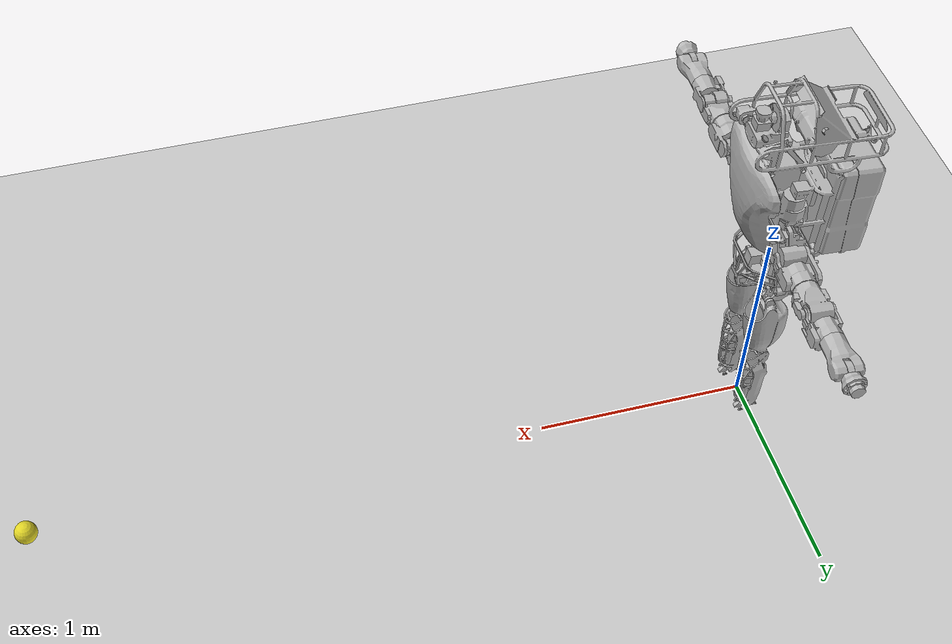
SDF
<sdf version="1.5">
 <world name="default">
  <physics name="default_physics" default="0" type="ode">
   <gravity>0 0 -9.81</gravity>
   <simbody>
    <accuracy>0.005</accuracy>
    <max_transient_velocity>0.005</max_transient_velocity>
    <contact><stiffness>1e+08</stiffness><dissipation>20</dissipation></contact>
   </simbody>
   <ode>
    <solver>
     <use_dynamic_moi_rescaling>1</use_dynamic_moi_rescaling>
     <type>quick</type>
     <iters>200</iters>
     <sor>1</sor>
    </solver>
    <constraints>
     <cfm>0</cfm>
     <erp>0.2</erp>
     <contact_max_correcting_vel>100</contact_max_correcting_vel>
     <contact_surface_layer>0</contact_surface_layer>
    </constraints>
   </ode>
   <real_time_update_rate>1000</real_time_update_rate>
   <max_step_size>0.001</max_step_size>
   <real_time_factor>1</real_time_factor>
   <magnetic_field>5.5645e-06 2.28758e-05 -4.23884e-05</magnetic_field>
  </physics>
  <light name="sun" type="directional">
   <pose>0 0 10 0 -0 0</pose>
   <diffuse>0.8 0.8 0.8 1</diffuse>
   <specular>0.2 0.2 0.2 1</specular>
   <attenuation>
    <range>1000</range>
    <constant>0.9</constant>
    <linear>0.01</linear>
    <quadratic>0.001</quadratic>
   </attenuation>
   <direction>-0.5 0.1 -0.9</direction>
  </light>
  <model name="ground_plane">
   <static>1</static>
   <link name="link">
    <collision name="collision">
     <geometry><plane><normal>0 0 1</normal><size>100 100</size></plane></geometry>
     <surface><friction><ode><mu>100</mu><mu2>50</mu2></ode></friction></surface>
    </collision>
    <visual name="visual">
     <cast_shadows>0</cast_shadows>
     <geometry><plane><normal>0 0 1</normal><size>100 100</size></plane></geometry>
     <material>
      <script><uri>file://media/materials/scripts/gazebo.material</uri><name>Gazebo/Grey</name></script>
     </material>
    </visual>
   </link>
  </model>
  <plugin name="vrc_plugin" filename="libVRCPlugin.so">
   <atlas><model_name>atlas</model_name><pin_link>utorso</pin_link></atlas>
   <drc_vehicle><model_name>golf_cart</model_name><seat_link>chassis</seat_link></drc_vehicle>
   <drc_fire_hose>
    <fire_hose_model>fire_hose</fire_hose_model>
    <coupling_link>coupling</coupling_link>
    <standpipe_model>standpipe</standpipe_model>
    <spout_link>standpipe</spout_link>
    <thread_pitch>-1000</thread_pitch>
    <coupling_relative_pose>1.17038e-05 -0.125623 0.35 -0.0412152 -1.57078 1.61199</coupling_relative_pose>
   </drc_fire_hose>
  </plugin>
  <plugin name="vrc_scoring" filename="libVRCScoringPlugin.so"/>
  <scene><ambient>0.4 0.4 0.4 1</ambient><background>0.7 0.7 0.7 1</background><shadows>1</shadows></scene>
  <spherical_coordinates>
   <surface_model>EARTH_WGS84</surface_model>
   <latitude_deg>0</latitude_deg>
   <longitude_deg>0</longitude_deg>
   <elevation>0</elevation>
   <heading_deg>0</heading_deg>
  </spherical_coordinates>
  <model name="atlas">
   <link name="pelvis">
    <inertial>
     <pose>0.011608 0 0.0266707 0 -0 0</pose>
     <mass>9.609</mass>
     <inertia>
      <ixx>0.125568</ixx>
      <ixy>0.0008</ixy>
      <ixz>-0.000500733</ixz>
      <iyy>0.0972042</iyy>
      <iyz>-0.0005</iyz>
      <izz>0.117936</izz>
     </inertia>
    </inertial>
    <collision name="pelvis_collision">
     <pose>0.046 0 0.01 1.5708 -0 0</pose>
     <geometry><cylinder><length>0.06</length><radius>0.11</radius></cylinder></geometry>
     <surface><friction><ode><mu>0.9</mu><mu2>0.9</mu2></ode></friction></surface>
    </collision>
    <collision name="pelvis_collision_pelvis_1">
     <pose>-0.03 0 0.01 1.5708 -0 0</pose>
     <geometry><cylinder><length>0.06</length><radius>0.11</radius></cylinder></geometry>
     <surface><friction><ode><mu>0.9</mu><mu2>0.9</mu2></ode></friction></surface>
    </collision>
    <collision name="pelvis_collision_pelvis_2">
     <pose>0.01 0.042 0.09 0 -0 0</pose>
     <geometry><cylinder><length>0.05</length><radius>0.16</radius></cylinder></geometry>
     <surface><friction><ode><mu>0.9</mu><mu2>0.9</mu2></ode></friction></surface>
    </collision>
    <collision name="pelvis_collision_pelvis_3">
     <pose>0.01 -0.042 0.09 0 -0 0</pose>
     <geometry><cylinder><length>0.05</length><radius>0.16</radius></cylinder></geometry>
     <surface><friction><ode><mu>0.9</mu><mu2>0.9</mu2></ode></friction></surface>
    </collision>
    <collision name="pelvis_collision_pelvis_4">
     <pose>-0.1 0 -0.02 0 -0 0</pose>
     <geometry><box><size>0.1 0.15 0.2</size></box></geometry>
     <surface><friction><ode><mu>0.9</mu><mu2>0.9</mu2></ode></friction></surface>
    </collision>
    <visual name="pelvis_visual">
     <geometry>
      <mesh><scale>1 1 1</scale><uri>model://atlas_description/meshes_unplugged/pelvis.dae</uri></mesh>
     </geometry>
    </visual>
    <visual name="pelvis_visual_pelvis_1">
     <pose>0.0599153 0 -0.01415 0 -0 0</pose>
     <geometry><box><size>0.01 0.01 0.01</size></box></geometry>
    </visual>
    <sensor name="imu_sensor" type="imu">
     <always_on>1</always_on>
     <update_rate>1000</update_rate>
     <imu>
      <noise>
       <type>gaussian</type>
       <rate>
        <mean>0</mean>
        <stddev>0.0002</stddev>
        <bias_mean>7.5e-06</bias_mean>
        <bias_stddev>8e-07</bias_stddev>
       </rate>
       <accel><mean>0</mean><stddev>0.017</stddev><bias_mean>0.1</bias_mean><bias_stddev>0.001</bias_stddev></accel>
      </noise>
     </imu>
     <pose>0.0599153 0 -0.01415 0 -0 0</pose>
    </sensor>
   </link>
   <link name="ltorso">
    <pose>-0.0125 0 0 0 -0 0</pose>
    <inertial>
     <pose>-0.0112984 -3.15366e-06 0.0746835 0 -0 0</pose>
     <mass>2.27</mass>
     <inertia>
      <ixx>0.0039092</ixx>
      <ixy>-5.04491e-08</ixy>
      <ixz>-0.000342157</ixz>
      <iyy>0.00341694</iyy>
      <iyz>4.87119e-07</iyz>
      <izz>0.00174492</izz>
     </inertia>
    </inertial>
    <visual name="ltorso_visual">
     <geometry>
      <mesh><scale>1 1 1</scale><uri>model://atlas_description/meshes_unplugged/ltorso.dae</uri></mesh>
     </geometry>
    </visual>
   </link>
   <joint name="back_bkz" type="revolute">
    <child>ltorso</child>
    <parent>pelvis</parent>
    <axis>
     <xyz>0 0 1</xyz>
     <limit><lower>-0.663225</lower><upper>0.663225</upper><effort>106</effort><velocity>12</velocity></limit>
     <dynamics>
      <damping>0.1</damping>
      <friction>0</friction>
      <spring_reference>0</spring_reference>
      <spring_stiffness>0</spring_stiffness>
     </dynamics>
     <use_parent_model_frame>1</use_parent_model_frame>
    </axis>
    <physics>
     <ode>
      <implicit_spring_damper>1</implicit_spring_damper>
      <cfm_damping>1</cfm_damping>
      <limit><cfm>0</cfm><erp>0.2</erp></limit>
     </ode>
    </physics>
   </joint>
   <link name="mtorso">
    <pose>-0.0125 0 0.162 0 -0 0</pose>
    <inertial>
     <pose>-0.00816266 -0.0131245 0.0305974 0 -0 0</pose>
     <mass>0.799</mass>
     <inertia>
      <ixx>0.000454181</ixx>
      <ixy>-6.10764e-05</ixy>
      <ixz>3.94009e-05</ixz>
      <iyy>0.000483282</iyy>
      <iyz>5.27463e-05</iyz>
      <izz>0.000444215</izz>
     </inertia>
    </inertial>
    <collision name="mtorso_collision">
     <pose>0 0 -0.02 0 -0 0</pose>
     <geometry><cylinder><length>0.15</length><radius>0.02</radius></cylinder></geometry>
     <surface><friction><ode><mu>0.9</mu><mu2>0.9</mu2></ode></friction></surface>
    </collision>
    <visual name="mtorso_visual">
     <geometry>
      <mesh><scale>1 1 1</scale><uri>model://atlas_description/meshes_unplugged/mtorso.dae</uri></mesh>
     </geometry>
    </visual>
   </link>
   <joint name="back_bky" type="revolute">
    <child>mtorso</child>
    <parent>ltorso</parent>
    <axis>
     <xyz>0 1 0</xyz>
     <limit><lower>-0.219388</lower><upper>0.538783</upper><effort>445</effort><velocity>9</velocity></limit>
     <dynamics>
      <damping>0.1</damping>
      <friction>0</friction>
      <spring_reference>0</spring_reference>
      <spring_stiffness>0</spring_stiffness>
     </dynamics>
     <use_parent_model_frame>1</use_parent_model_frame>
    </axis>
    <physics>
     <ode>
      <implicit_spring_damper>1</implicit_spring_damper>
      <cfm_damping>1</cfm_damping>
      <limit><cfm>0</cfm><erp>0.2</erp></limit>
     </ode>
    </physics>
   </joint>
   <link name="utorso">
    <pose>-0.0125 0 0.212 0 -0 0</pose>
    <inertial>
     <pose>-0.0616866 0.00229456 0.316809 0 -0 0</pose>
     <mass>84.609</mass>
     <inertia>
      <ixx>1.62389</ixx>
      <ixy>-0.0319003</ixy>
      <ixz>0.0816618</ixz>
      <iyy>1.65538</iyy>
      <iyz>0.0472154</iyz>
      <izz>0.577362</izz>
     </inertia>
    </inertial>
    <collision name="utorso_collision">
     <pose>-0.102 0 0.25 0 -0 0</pose>
     <geometry><box><size>0.4 0.35 0.5</size></box></geometry>
     <surface><friction><ode><mu>0.9</mu><mu2>0.9</mu2></ode></friction></surface>
    </collision>
    <collision name="utorso_collision_utorso_1">
     <pose>0.2 0 0.46 0 1.5707 0</pose>
     <geometry><box><size>0.13 0.5 0.1</size></box></geometry>
     <surface><friction><ode><mu>0.9</mu><mu2>0.9</mu2></ode></friction></surface>
    </collision>
    <collision name="utorso_collision_utorso_2">
     <pose>0.2 0 0.285 3.14159 1.44159 3.14159</pose>
     <geometry><box><size>0.2 0.23 0.1</size></box></geometry>
     <surface><friction><ode><mu>0.9</mu><mu2>0.9</mu2></ode></friction></surface>
    </collision>
    <collision name="utorso_collision_utorso_3">
     <pose>0.15 0 0.1 3.14159 1.14159 3.14159</pose>
     <geometry><box><size>0.2 0.18 0.1</size></box></geometry>
     <surface><friction><ode><mu>0.9</mu><mu2>0.9</mu2></ode></friction></surface>
    </collision>
    <collision name="utorso_collision_utorso_4">
     <pose>-0.035 0 0.6265 0 -0 0</pose>
     <geometry><box><size>0.506306 0.341719 0.12</size></box></geometry>
     <surface><friction><ode><mu>0.9</mu><mu2>0.9</mu2></ode></friction></surface>
    </collision>
    <collision name="utorso_collision_utorso_5">
     <pose>0.208 0 0.8215 1.5707 -0 0</pose>
     <geometry><cylinder><length>0.13</length><radius>0.008</radius></cylinder></geometry>
     <surface><friction><ode><mu>0.9</mu><mu2>0.9</mu2></ode></friction></surface>
    </collision>
    <collision name="utorso_collision_utorso_6">
     <pose>0.208 -0.125 0.745 -0.38535 0 0</pose>
     <geometry><cylinder><length>0.15</length><radius>0.008</radius></cylinder></geometry>
     <surface><friction><ode><mu>0.9</mu><mu2>0.9</mu2></ode></friction></surface>
    </collision>
    <collision name="utorso_collision_utorso_7">
     <pose>0.208 0.125 0.745 0.38535 -0 0</pose>
     <geometry><cylinder><length>0.15</length><radius>0.008</radius></cylinder></geometry>
     <surface><friction><ode><mu>0.9</mu><mu2>0.9</mu2></ode></friction></surface>
    </collision>
    <collision name="utorso_collision_utorso_8">
     <pose>0.063 -0.125 0.745 -0.38535 0 0</pose>
     <geometry><cylinder><length>0.15</length><radius>0.008</radius></cylinder></geometry>
     <surface><friction><ode><mu>0.9</mu><mu2>0.9</mu2></ode></friction></surface>
    </collision>
    <collision name="utorso_collision_utorso_9">
     <pose>0.063 0.125 0.745 0.38535 -0 0</pose>
     <geometry><cylinder><length>0.15</length><radius>0.008</radius></cylinder></geometry>
     <surface><friction><ode><mu>0.9</mu><mu2>0.9</mu2></ode></friction></surface>
    </collision>
    <collision name="utorso_collision_utorso_10">
     <pose>0.14 0.06 0.8215 1.5707 5.55112e-17 1.5707</pose>
     <geometry><cylinder><length>0.15</length><radius>0.008</radius></cylinder></geometry>
     <surface><friction><ode><mu>0.9</mu><mu2>0.9</mu2></ode></friction></surface>
    </collision>
    <collision name="utorso_collision_utorso_11">
     <pose>0.14 -0.06 0.8215 1.5707 5.55112e-17 1.5707</pose>
     <geometry><cylinder><length>0.15</length><radius>0.008</radius></cylinder></geometry>
     <surface><friction><ode><mu>0.9</mu><mu2>0.9</mu2></ode></friction></surface>
    </collision>
    <collision name="utorso_collision_utorso_12">
     <pose>-0.029 0 0.731 0 -0.65 0</pose>
     <geometry><box><size>0.2 0.25 0.01</size></box></geometry>
     <surface><friction><ode><mu>0.9</mu><mu2>0.9</mu2></ode></friction></surface>
    </collision>
    <collision name="utorso_collision_utorso_13">
     <pose>0.063 0 0.8215 1.5707 -0 0</pose>
     <geometry><cylinder><length>0.13</length><radius>0.008</radius></cylinder></geometry>
     <surface><friction><ode><mu>0.9</mu><mu2>0.9</mu2></ode></friction></surface>
    </collision>
    <collision name="utorso_collision_utorso_14">
     <pose>0.261 0.156 0.6215 1.5707 -0 0</pose>
     <geometry><cylinder><length>0.016</length><radius>0.055</radius></cylinder></geometry>
     <surface><friction><ode><mu>0.9</mu><mu2>0.9</mu2></ode></friction></surface>
    </collision>
    <collision name="utorso_collision_utorso_15">
     <pose>0.261 -0.156 0.6215 1.5707 -0 0</pose>
     <geometry><cylinder><length>0.016</length><radius>0.055</radius></cylinder></geometry>
     <surface><friction><ode><mu>0.9</mu><mu2>0.9</mu2></ode></friction></surface>
    </collision>
    <visual name="utorso_visual">
     <geometry>
      <mesh><scale>1 1 1</scale><uri>model://atlas_description/meshes_unplugged/utorso.dae</uri></mesh>
     </geometry>
    </visual>
    <visual name="utorso_visual_utorso_1">
     <pose>0.155 0.121 0.785 0 -0 1.309</pose>
     <geometry><box><size>0.01 0.01 0.01</size></box></geometry>
    </visual>
    <visual name="utorso_visual_utorso_2">
     <pose>0.155 -0.121 0.785 0 0 -1.309</pose>
     <geometry><box><size>0.01 0.01 0.01</size></box></geometry>
    </visual>
    <sensor name="l_situational_awareness_camera_sensor" type="camera">
     <update_rate>60</update_rate>
     <camera name="l_situational_awareness_camera">
      <horizontal_fov>2</horizontal_fov>
      <image><width>1280</width><height>1024</height><format>R8G8B8</format></image>
      <clip><near>0.02</near><far>300</far></clip>
      <noise><type>gaussian</type><mean>0</mean><stddev>0.007</stddev></noise>
     </camera>
     <plugin name="l_situational_awareness_camera_controller" filename="libgazebo_ros_camera.so">
      <alwaysOn>true</alwaysOn>
      <updateRate>0.0</updateRate>
      <cameraName>l_situational_awareness_camera</cameraName>
      <imageTopicName>image_raw</imageTopicName>
      <cameraInfoTopicName>camera_info</cameraInfoTopicName>
      <frameName>l_situational_awareness_camera_optical_frame</frameName>
      <hackBaseline>0.0</hackBaseline>
      <distortionK1>0.0</distortionK1>
      <distortionK2>0.0</distortionK2>
      <distortionK3>0.0</distortionK3>
      <distortionT1>0.0</distortionT1>
      <distortionT2>0.0</distortionT2>
     </plugin>
     <pose>0.155 0.121 0.785 0 -0 1.309</pose>
    </sensor>
    <sensor name="r_situational_awareness_camera_sensor" type="camera">
     <update_rate>60</update_rate>
     <camera name="r_situational_awareness_camera">
      <horizontal_fov>2</horizontal_fov>
      <image><width>1280</width><height>1024</height><format>R8G8B8</format></image>
      <clip><near>0.02</near><far>300</far></clip>
      <noise><type>gaussian</type><mean>0</mean><stddev>0.007</stddev></noise>
     </camera>
     <plugin name="r_situational_awareness_camera_controller" filename="libgazebo_ros_camera.so">
      <alwaysOn>true</alwaysOn>
      <updateRate>0.0</updateRate>
      <cameraName>r_situational_awareness_camera</cameraName>
      <imageTopicName>image_raw</imageTopicName>
      <cameraInfoTopicName>camera_info</cameraInfoTopicName>
      <frameName>r_situational_awareness_camera_optical_frame</frameName>
      <hackBaseline>0.0</hackBaseline>
      <distortionK1>0.0</distortionK1>
      <distortionK2>0.0</distortionK2>
      <distortionK3>0.0</distortionK3>
      <distortionT1>0.0</distortionT1>
      <distortionT2>0.0</distortionT2>
     </plugin>
     <pose>0.155 -0.121 0.785 0 0 -1.309</pose>
    </sensor>
   </link>
   <joint name="back_bkx" type="revolute">
    <child>utorso</child>
    <parent>mtorso</parent>
    <axis>
     <xyz>1 0 0</xyz>
     <limit><lower>-0.523599</lower><upper>0.523599</upper><effort>300</effort><velocity>12</velocity></limit>
     <dynamics>
      <damping>0.1</damping>
      <friction>0</friction>
      <spring_reference>0</spring_reference>
      <spring_stiffness>0</spring_stiffness>
     </dynamics>
     <use_parent_model_frame>1</use_parent_model_frame>
    </axis>
    <physics>
     <ode>
      <implicit_spring_damper>1</implicit_spring_damper>
      <cfm_damping>1</cfm_damping>
      <limit><cfm>0</cfm><erp>0.2</erp></limit>
     </ode>
    </physics>
   </joint>
   <link name="l_clav">
    <pose>0.1281 0.2256 0.6896 0 -0 -3.14159</pose>
    <inertial>
     <pose>0 0 -0.084 0 -0 0</pose>
     <mass>4.466</mass>
     <inertia><ixx>0.011</ixx><ixy>0</ixy><ixz>0</ixz><iyy>0.009</iyy><iyz>0.004</iyz><izz>0.004</izz></inertia>
    </inertial>
    <collision name="l_clav_collision">
     <pose>0 -0.11 -0.248 -2.65359e-06 1.57079 -2.65359e-06</pose>
     <geometry><cylinder><length>0.1525</length><radius>0.0555</radius></cylinder></geometry>
     <surface><friction><ode><mu>0.9</mu><mu2>0.9</mu2></ode></friction></surface>
    </collision>
    <collision name="l_clav_collision_l_clav_1">
     <pose>0.005 -0.015 -0.08 0 -0 0</pose>
     <geometry><cylinder><length>0.26</length><radius>0.067</radius></cylinder></geometry>
     <surface><friction><ode><mu>0.9</mu><mu2>0.9</mu2></ode></friction></surface>
    </collision>
    <collision name="l_clav_collision_l_clav_2">
     <pose>0.004 -0.064 -0.247 1.05 -0 0</pose>
     <geometry><box><size>0.1 0.07 0.072</size></box></geometry>
     <surface><friction><ode><mu>0.9</mu><mu2>0.9</mu2></ode></friction></surface>
    </collision>
    <visual name="l_clav_visual">
     <geometry>
      <mesh><scale>1 1 1</scale><uri>model://atlas_description/meshes_unplugged/r_clav.dae</uri></mesh>
     </geometry>
    </visual>
   </link>
   <joint name="l_arm_shz" type="revolute">
    <child>l_clav</child>
    <parent>utorso</parent>
    <axis>
     <xyz>0 0 1</xyz>
     <limit><lower>-1.5708</lower><upper>0.785398</upper><effort>87</effort><velocity>12</velocity></limit>
     <dynamics>
      <damping>0.1</damping>
      <friction>0</friction>
      <spring_reference>0</spring_reference>
      <spring_stiffness>0</spring_stiffness>
     </dynamics>
     <use_parent_model_frame>1</use_parent_model_frame>
    </axis>
    <physics>
     <ode>
      <implicit_spring_damper>1</implicit_spring_damper>
      <cfm_damping>1</cfm_damping>
      <limit><cfm>0</cfm><erp>0.2</erp></limit>
     </ode>
    </physics>
   </joint>
   <link name="l_scap">
    <pose>0.1281 0.3356 0.4446 0 -0 -3.14159</pose>
    <inertial>
     <mass>3.899</mass>
     <inertia><ixx>0.00319</ixx><ixy>0</ixy><ixz>0</ixz><iyy>0.00583</iyy><iyz>0</iyz><izz>0.00583</izz></inertia>
    </inertial>
    <collision name="l_scap_collision">
     <pose>-0.005 -0.115 -0.014 1.5708 -0 0</pose>
     <geometry><cylinder><length>0.105</length><radius>0.057</radius></cylinder></geometry>
     <surface><friction><ode><mu>0.9</mu><mu2>0.9</mu2></ode></friction></surface>
    </collision>
    <collision name="l_scap_collision_l_scap_1">
     <pose>-0.005 -0.075 -0.015 0 -0 0</pose>
     <geometry><box><size>0.16 0.17 0.08</size></box></geometry>
     <surface><friction><ode><mu>0.9</mu><mu2>0.9</mu2></ode></friction></surface>
    </collision>
    <collision name="l_scap_collision_l_scap_2">
     <pose>0.076 -0.0615 0.0128 2.25 -0 0</pose>
     <geometry><box><size>0.02 0.029 0.018</size></box></geometry>
     <surface><friction><ode><mu>0.9</mu><mu2>0.9</mu2></ode></friction></surface>
    </collision>
    <collision name="l_scap_collision_l_scap_3">
     <pose>-0.075 0.015 0.019 1 -0 0</pose>
     <geometry><box><size>0.028 0.09 0.05</size></box></geometry>
     <surface><friction><ode><mu>0.9</mu><mu2>0.9</mu2></ode></friction></surface>
    </collision>
    <visual name="l_scap_visual">
     <geometry>
      <mesh><scale>1 1 1</scale><uri>model://atlas_description/meshes_unplugged/r_scap.dae</uri></mesh>
     </geometry>
    </visual>
   </link>
   <joint name="l_arm_shx" type="revolute">
    <child>l_scap</child>
    <parent>l_clav</parent>
    <axis>
     <xyz>1 0 0</xyz>
     <limit><lower>-1.5708</lower><upper>1.5708</upper><effort>99</effort><velocity>12</velocity></limit>
     <dynamics>
      <damping>0.1</damping>
      <friction>0</friction>
      <spring_reference>0</spring_reference>
      <spring_stiffness>0</spring_stiffness>
     </dynamics>
     <use_parent_model_frame>1</use_parent_model_frame>
    </axis>
    <physics>
     <ode>
      <implicit_spring_damper>1</implicit_spring_damper>
      <cfm_damping>1</cfm_damping>
      <limit><cfm>0</cfm><erp>0.2</erp></limit>
     </ode>
    </physics>
   </joint>
   <link name="l_uarm">
    <pose>0.1281 0.5226 0.4286 0 -0 -3.14159</pose>
    <inertial>
     <pose>0 0.065 0 0 -0 0</pose>
     <mass>4.386</mass>
     <inertia><ixx>0.00656</ixx><ixy>0</ixy><ixz>0</ixz><iyy>0.00358</iyy><iyz>0</iyz><izz>0.00656</izz></inertia>
    </inertial>
    <collision name="l_uarm_collision">
     <pose>0 -0.035 -0.005 1.5708 -0 0</pose>
     <geometry><cylinder><length>0.11</length><radius>0.065</radius></cylinder></geometry>
     <surface><friction><ode><mu>0.9</mu><mu2>0.9</mu2></ode></friction></surface>
    </collision>
    <collision name="l_uarm_collision_l_uarm_1">
     <pose>-0.01 -0.043 0.002 -2.65359e-06 1.57079 -2.65359e-06</pose>
     <geometry><box><size>0.05 0.07 0.15</size></box></geometry>
     <surface><friction><ode><mu>0.9</mu><mu2>0.9</mu2></ode></friction></surface>
    </collision>
    <visual name="l_uarm_visual">
     <geometry>
      <mesh><scale>1 1 1</scale><uri>model://atlas_description/meshes_unplugged/r_uarm.dae</uri></mesh>
     </geometry>
    </visual>
   </link>
   <joint name="l_arm_ely" type="revolute">
    <child>l_uarm</child>
    <parent>l_scap</parent>
    <axis>
     <xyz>-0 1 0</xyz>
     <limit><lower>0</lower><upper>3.14159</upper><effort>63</effort><velocity>12</velocity></limit>
     <dynamics>
      <damping>0.1</damping>
      <friction>0</friction>
      <spring_reference>0</spring_reference>
      <spring_stiffness>0</spring_stiffness>
     </dynamics>
     <use_parent_model_frame>1</use_parent_model_frame>
    </axis>
    <physics>
     <ode>
      <implicit_spring_damper>1</implicit_spring_damper>
      <cfm_damping>1</cfm_damping>
      <limit><cfm>0</cfm><erp>0.2</erp></limit>
     </ode>
    </physics>
   </joint>
   <link name="l_larm">
    <pose>0.1281 0.6416 0.4378 0 -0 -3.14159</pose>
    <inertial>
     <mass>3.248</mass>
     <inertia><ixx>0.00265</ixx><ixy>0</ixy><ixz>0</ixz><iyy>0.00446</iyy><iyz>0</iyz><izz>0.00446</izz></inertia>
    </inertial>
    <collision name="l_larm_collision">
     <pose>0 -0.075 -0.01 -1.5708 0 0</pose>
     <geometry><cylinder><length>0.04</length><radius>0.051</radius></cylinder></geometry>
     <surface><friction><ode><mu>0.9</mu><mu2>0.9</mu2></ode></friction></surface>
    </collision>
    <collision name="l_larm_collision_l_larm_1">
     <pose>-0.012 0 0.0025 -2.65359e-06 1.57079 -2.65359e-06</pose>
     <geometry><cylinder><length>0.147</length><radius>0.045</radius></cylinder></geometry>
     <surface><friction><ode><mu>0.9</mu><mu2>0.9</mu2></ode></friction></surface>
    </collision>
    <collision name="l_larm_collision_l_larm_2">
     <pose>-0.07 -0.077 -0.015 0 -0 0</pose>
     <geometry><box><size>0.025 0.155 0.07</size></box></geometry>
     <surface><friction><ode><mu>0.9</mu><mu2>0.9</mu2></ode></friction></surface>
    </collision>
    <collision name="l_larm_collision_l_larm_3">
     <pose>0.05 -0.067 -0.009 0 -0 0</pose>
     <geometry><box><size>0.025 0.06 0.06</size></box></geometry>
     <surface><friction><ode><mu>0.9</mu><mu2>0.9</mu2></ode></friction></surface>
    </collision>
    <collision name="l_larm_collision_l_larm_4">
     <pose>-0.032 -0.071 -0.06 0 -0 0</pose>
     <geometry><box><size>0.04 0.115 0.05</size></box></geometry>
     <surface><friction><ode><mu>0.9</mu><mu2>0.9</mu2></ode></friction></surface>
    </collision>
    <collision name="l_larm_collision_l_larm_5">
     <pose>0.03 0.01 -0.05 0 -0 0</pose>
     <geometry><box><size>0.045 0.055 0.023</size></box></geometry>
     <surface><friction><ode><mu>0.9</mu><mu2>0.9</mu2></ode></friction></surface>
    </collision>
    <visual name="l_larm_visual">
     <geometry>
      <mesh><scale>1 1 1</scale><uri>model://atlas_description/meshes_unplugged/r_larm.dae</uri></mesh>
     </geometry>
    </visual>
   </link>
   <joint name="l_arm_elx" type="revolute">
    <child>l_larm</child>
    <parent>l_uarm</parent>
    <axis>
     <xyz>1 0 0</xyz>
     <limit><lower>0</lower><upper>2.35619</upper><effort>112</effort><velocity>12</velocity></limit>
     <dynamics>
      <damping>0.1</damping>
      <friction>0</friction>
      <spring_reference>0</spring_reference>
      <spring_stiffness>0</spring_stiffness>
     </dynamics>
     <use_parent_model_frame>1</use_parent_model_frame>
    </axis>
    <physics>
     <ode>
      <implicit_spring_damper>1</implicit_spring_damper>
      <cfm_damping>1</cfm_damping>
      <limit><cfm>0</cfm><erp>0.2</erp></limit>
     </ode>
    </physics>
   </joint>
   <link name="l_ufarm">
    <pose>0.1281 0.94115 0.42859 3.14159 -2.06823e-13 2.06823e-13</pose>
    <inertial>
     <pose>0.00015 0.08296 0.00037 0 -0 0</pose>
     <mass>2.4798</mass>
     <inertia>
      <ixx>0.012731</ixx>
      <ixy>0</ixy>
      <ixz>0</ixz>
      <iyy>0.002857</iyy>
      <iyz>0</iyz>
      <izz>0.011948</izz>
     </inertia>
    </inertial>
    <collision name="l_ufarm_collision">
     <pose>0 0.15 0 1.57 -0 0</pose>
     <geometry><cylinder><length>0.1</length><radius>0.053</radius></cylinder></geometry>
     <surface><friction><ode><mu>0.9</mu><mu2>0.9</mu2></ode></friction></surface>
    </collision>
    <collision name="l_ufarm_collision_l_ufarm_1">
     <pose>-0.001 0.07 0 -2.65359e-06 1.57079 -2.65359e-06</pose>
     <geometry><box><size>0.08 0.09 0.11</size></box></geometry>
     <surface><friction><ode><mu>0.9</mu><mu2>0.9</mu2></ode></friction></surface>
    </collision>
    <collision name="l_ufarm_collision_l_ufarm_2">
     <pose>0 0.005 0 0 1.57 0</pose>
     <geometry><cylinder><length>0.125</length><radius>0.04</radius></cylinder></geometry>
     <surface><friction><ode><mu>0.9</mu><mu2>0.9</mu2></ode></friction></surface>
    </collision>
    <visual name="l_ufarm_visual">
     <geometry>
      <mesh><scale>1 1 1</scale><uri>model://atlas_description/meshes_unplugged/r_farm.dae</uri></mesh>
     </geometry>
    </visual>
   </link>
   <joint name="l_arm_wry" type="revolute">
    <child>l_ufarm</child>
    <parent>l_larm</parent>
    <axis>
     <xyz>-0 1 0</xyz>
     <limit><lower>-3.011</lower><upper>3.011</upper><effort>25</effort><velocity>10</velocity></limit>
     <dynamics>
      <damping>0.1</damping>
      <friction>0</friction>
      <spring_reference>0</spring_reference>
      <spring_stiffness>0</spring_stiffness>
     </dynamics>
     <use_parent_model_frame>1</use_parent_model_frame>
    </axis>
    <physics>
     <ode>
      <implicit_spring_damper>1</implicit_spring_damper>
      <cfm_damping>1</cfm_damping>
      <limit><cfm>0</cfm><erp>0.2</erp></limit>
     </ode>
    </physics>
   </joint>
   <link name="l_lfarm">
    <pose>0.1281 0.94115 0.42859 3.14159 -2.06823e-13 2.06823e-13</pose>
    <inertial>
     <pose>0.00017 -0.02515 0.00163 0 -0 0</pose>
     <mass>0.648</mass>
     <inertia>
      <ixx>0.000764</ixx>
      <ixy>0</ixy>
      <ixz>0</ixz>
      <iyy>0.000429</iyy>
      <iyz>0</iyz>
      <izz>0.000825</izz>
     </inertia>
    </inertial>
    <collision name="l_lfarm_collision">
     <pose>0 -0.104 0 1.5708 -0 0</pose>
     <geometry><cylinder><length>0.02</length><radius>0.031</radius></cylinder></geometry>
     <surface><friction><ode><mu>0.9</mu><mu2>0.9</mu2></ode></friction></surface>
    </collision>
    <collision name="l_lfarm_collision_l_lfarm_1">
     <pose>0 -0.087 0 1.5708 -0 0</pose>
     <geometry><cylinder><length>0.015</length><radius>0.045</radius></cylinder></geometry>
     <surface><friction><ode><mu>0.9</mu><mu2>0.9</mu2></ode></friction></surface>
    </collision>
    <collision name="l_lfarm_collision_l_lfarm_2">
     <pose>0 -0.075 0 1.5708 -0 0</pose>
     <geometry><cylinder><length>0.015</length><radius>0.052</radius></cylinder></geometry>
     <surface><friction><ode><mu>0.9</mu><mu2>0.9</mu2></ode></friction></surface>
    </collision>
    <collision name="l_lfarm_collision_l_lfarm_3">
     <pose>0 -0.052 0 1.5708 -0 0</pose>
     <geometry><cylinder><length>0.027</length><radius>0.043</radius></cylinder></geometry>
     <surface><friction><ode><mu>0.9</mu><mu2>0.9</mu2></ode></friction></surface>
    </collision>
    <visual name="l_lfarm_visual">
     <pose>0 0 0 3.14159 -2.06823e-13 3.14159</pose>
     <geometry>
      <mesh><scale>1 1 1</scale><uri>model://atlas_description/meshes_unplugged/r_hand.dae</uri></mesh>
     </geometry>
    </visual>
   </link>
   <joint name="l_arm_wrx" type="revolute">
    <child>l_lfarm</child>
    <parent>l_ufarm</parent>
    <axis>
     <xyz>1 0 0</xyz>
     <limit><lower>-1.7628</lower><upper>1.7628</upper><effort>25</effort><velocity>10</velocity></limit>
     <dynamics>
      <damping>0.1</damping>
      <friction>0</friction>
      <spring_reference>0</spring_reference>
      <spring_stiffness>0</spring_stiffness>
     </dynamics>
     <use_parent_model_frame>1</use_parent_model_frame>
    </axis>
    <physics>
     <provide_feedback>1</provide_feedback>
     <ode>
      <provide_feedback>1</provide_feedback>
      <limit><cfm>0</cfm><erp>0.2</erp></limit>
      <implicit_spring_damper>1</implicit_spring_damper>
      <cfm_damping>1</cfm_damping>
     </ode>
    </physics>
   </joint>
   <link name="l_hand">
    <pose>0.1281 0.94115 0.42859 0 4.13646e-13 -3.14159</pose>
    <inertial>
     <pose>0.00016 -0.08159 2e-05 0 -0 0</pose>
     <mass>0.5839</mass>
     <inertia>
      <ixx>0.000388</ixx>
      <ixy>0</ixy>
      <ixz>0</ixz>
      <iyy>0.000477</iyy>
      <iyz>0</iyz>
      <izz>0.000379</izz>
     </inertia>
    </inertial>
   </link>
   <joint name="l_arm_wry2" type="revolute">
    <child>l_hand</child>
    <parent>l_lfarm</parent>
    <axis>
     <xyz>0 -1 0</xyz>
     <limit><lower>-2.9671</lower><upper>2.9671</upper><effort>25</effort><velocity>10</velocity></limit>
     <dynamics>
      <damping>0.1</damping>
      <friction>0</friction>
      <spring_reference>0</spring_reference>
      <spring_stiffness>0</spring_stiffness>
     </dynamics>
     <use_parent_model_frame>1</use_parent_model_frame>
    </axis>
    <physics>
     <ode>
      <implicit_spring_damper>1</implicit_spring_damper>
      <cfm_damping>1</cfm_damping>
      <limit><cfm>0</cfm><erp>0.2</erp></limit>
     </ode>
    </physics>
   </joint>
   <link name="head">
    <pose>0.2421 0 0.8335 0 -0 0</pose>
    <inertial>
     <pose>-0.0754942 3.38765e-05 0.0277411 0 -0 0</pose>
     <mass>1.41991</mass>
     <inertia>
      <ixx>0.00397627</ixx>
      <ixy>-1.51324e-06</ixy>
      <ixz>-0.000892818</ixz>
      <iyy>0.00412515</iyy>
      <iyz>-6.83342e-07</iyz>
      <izz>0.00353178</izz>
     </inertia>
    </inertial>
    <collision name="head_collision">
     <pose>-0.0503 0 -0.00195 0 -0 0</pose>
     <geometry><box><size>0.1311 0.12 0.0591</size></box></geometry>
     <surface><friction><ode><mu>0.9</mu><mu2>0.9</mu2></ode></friction></surface>
    </collision>
    <collision name="head_collision_head_1">
     <pose>-0.093 0 0.0868 0 -0 0</pose>
     <geometry><box><size>0.0468 0.12 0.1184</size></box></geometry>
     <surface><friction><ode><mu>0.9</mu><mu2>0.9</mu2></ode></friction></surface>
    </collision>
    <visual name="head_visual">
     <geometry>
      <mesh><scale>1 1 1</scale><uri>model://multisense_sl_description/meshes/head.dae</uri></mesh>
     </geometry>
    </visual>
    <visual name="head_visual_head_1">
     <pose>-0.0475 0.035 0 0 -0 0</pose>
     <geometry><box><size>0.01 0.01 0.01</size></box></geometry>
    </visual>
    <sensor name="head_imu_sensor" type="imu">
     <always_on>1</always_on>
     <update_rate>1000</update_rate>
     <imu>
      <noise>
       <type>gaussian</type>
       <rate>
        <mean>0</mean>
        <stddev>0.0002</stddev>
        <bias_mean>7.5e-06</bias_mean>
        <bias_stddev>8e-07</bias_stddev>
       </rate>
       <accel><mean>0</mean><stddev>0.017</stddev><bias_mean>0.1</bias_mean><bias_stddev>0.001</bias_stddev></accel>
      </noise>
     </imu>
     <pose>-0.0475 0.035 0 0 -0 0</pose>
    </sensor>
    <sensor name="stereo_camera" type="multicamera">
     <update_rate>10</update_rate>
     <camera name="left">
      <horizontal_fov>1.39626</horizontal_fov>
      <image><width>1024</width><height>544</height><format>R8G8B8</format></image>
      <clip><near>0.02</near><far>300</far></clip>
      <noise><type>gaussian</type><mean>0</mean><stddev>0.007</stddev></noise>
     </camera>
     <camera name="right">
      <pose>0 -0.07 0 0 -0 0</pose>
      <horizontal_fov>1.39626</horizontal_fov>
      <image><width>1024</width><height>544</height><format>R8G8B8</format></image>
      <clip><near>0.02</near><far>300</far></clip>
      <noise><type>gaussian</type><mean>0</mean><stddev>0.007</stddev></noise>
     </camera>
     <plugin name="stereo_camera_controller" filename="libgazebo_ros_multicamera.so">
      <alwaysOn>true</alwaysOn>
      <updateRate>0.0</updateRate>
      <cameraName>multisense/camera</cameraName>
      <imageTopicName>image_raw</imageTopicName>
      <cameraInfoTopicName>camera_info</cameraInfoTopicName>
      <frameName>left_camera_optical_frame</frameName>
      <hackBaseline>0.07</hackBaseline>
      <distortionK1>0.0</distortionK1>
      <distortionK2>0.0</distortionK2>
      <distortionK3>0.0</distortionK3>
      <distortionT1>0.0</distortionT1>
      <distortionT2>0.0</distortionT2>
     </plugin>
     <pose>0 0.035 -0.002 0 -0 0</pose>
    </sensor>
   </link>
   <joint name="neck_ry" type="revolute">
    <child>head</child>
    <parent>utorso</parent>
    <axis>
     <xyz>0 1 0</xyz>
     <limit><lower>-0.602139</lower><upper>1.14319</upper><effort>25</effort><velocity>6.28</velocity></limit>
     <dynamics>
      <damping>0.1</damping>
      <friction>0</friction>
      <spring_reference>0</spring_reference>
      <spring_stiffness>0</spring_stiffness>
     </dynamics>
     <use_parent_model_frame>1</use_parent_model_frame>
    </axis>
    <physics>
     <ode>
      <implicit_spring_damper>1</implicit_spring_damper>
      <cfm_damping>1</cfm_damping>
      <limit><cfm>0</cfm><erp>0.2</erp></limit>
     </ode>
    </physics>
   </joint>
   <link name="hokuyo_link">
    <pose>0.1975 0 0.9215 0 -0 0</pose>
    <inertial>
     <pose>0.0324349 0.0004084 -0.0041783 0 -0 0</pose>
     <mass>0.057664</mass>
     <inertia>
      <ixx>3.8183e-05</ixx>
      <ixy>4.9927e-08</ixy>
      <ixz>1.1003e-05</ixz>
      <iyy>4.3437e-05</iyy>
      <iyz>-9.8165e-09</iyz>
      <izz>4.2686e-05</izz>
     </inertia>
    </inertial>
    <collision name="hokuyo_link_collision">
     <pose>0.01885 0 -0.02119 0 -0 0</pose>
     <geometry><box><size>0.08 0.06 0.04238</size></box></geometry>
     <surface><friction><ode><mu>0.9</mu><mu2>0.9</mu2></ode></friction></surface>
    </collision>
    <collision name="hokuyo_link_collision_hokuyo_link_1">
     <pose>0.03 0 0.0235 0 -0 0</pose>
     <geometry><cylinder><length>0.047</length><radius>0.024425</radius></cylinder></geometry>
     <surface><friction><ode><mu>0.9</mu><mu2>0.9</mu2></ode></friction></surface>
    </collision>
    <visual name="hokuyo_link_visual">
     <pose>0.045 -0.0261018 -0.0834237 -0.314 0 0</pose>
     <geometry>
      <mesh><scale>1 1 1</scale><uri>model://multisense_sl_description/meshes/head_camera.dae</uri></mesh>
     </geometry>
    </visual>
    <sensor name="head_hokuyo_sensor" type="gpu_ray">
     <visualize>0</visualize>
     <update_rate>40</update_rate>
     <ray>
      <scan>
       <horizontal>
        <samples>1081</samples>
        <resolution>1</resolution>
        <min_angle>-2.35619</min_angle>
        <max_angle>2.35619</max_angle>
       </horizontal>
      </scan>
      <range><min>0.1</min><max>30</max><resolution>0.01</resolution></range>
      <noise><type>gaussian</type><mean>0</mean><stddev>0.01</stddev></noise>
     </ray>
     <plugin name="gazebo_ros_head_hokuyo_controller" filename="libgazebo_ros_gpu_laser.so">
      <topicName>/multisense/lidar_scan</topicName>
      <frameName>head_hokuyo_frame</frameName>
     </plugin>
     <pose>0.03 0 0.015 0 -0 0</pose>
    </sensor>
   </link>
   <joint name="hokuyo_joint" type="revolute">
    <child>hokuyo_link</child>
    <parent>head</parent>
    <axis>
     <xyz>1 0 0</xyz>
     <limit><lower>-1e+16</lower><upper>1e+16</upper></limit>
     <dynamics>
      <damping>0.01</damping>
      <friction>0</friction>
      <spring_reference>0</spring_reference>
      <spring_stiffness>0</spring_stiffness>
     </dynamics>
     <use_parent_model_frame>1</use_parent_model_frame>
    </axis>
    <physics>
     <ode>
      <implicit_spring_damper>1</implicit_spring_damper>
      <cfm_damping>1</cfm_damping>
      <limit><cfm>0</cfm><erp>0.2</erp></limit>
     </ode>
    </physics>
   </joint>
   <link name="r_clav">
    <pose>0.1281 -0.2256 0.6896 0 -0 0</pose>
    <inertial>
     <pose>0 0 -0.084 0 -0 0</pose>
     <mass>4.466</mass>
     <inertia><ixx>0.011</ixx><ixy>0</ixy><ixz>0</ixz><iyy>0.009</iyy><iyz>0.004</iyz><izz>0.004</izz></inertia>
    </inertial>
    <collision name="r_clav_collision">
     <pose>0 -0.11 -0.248 -2.65359e-06 1.57079 -2.65359e-06</pose>
     <geometry><cylinder><length>0.1525</length><radius>0.0555</radius></cylinder></geometry>
     <surface><friction><ode><mu>0.9</mu><mu2>0.9</mu2></ode></friction></surface>
    </collision>
    <collision name="r_clav_collision_r_clav_1">
     <pose>0.005 -0.015 -0.08 0 -0 0</pose>
     <geometry><cylinder><length>0.26</length><radius>0.067</radius></cylinder></geometry>
     <surface><friction><ode><mu>0.9</mu><mu2>0.9</mu2></ode></friction></surface>
    </collision>
    <collision name="r_clav_collision_r_clav_2">
     <pose>0.004 -0.064 -0.247 1.05 -0 0</pose>
     <geometry><box><size>0.1 0.07 0.072</size></box></geometry>
     <surface><friction><ode><mu>0.9</mu><mu2>0.9</mu2></ode></friction></surface>
    </collision>
    <visual name="r_clav_visual">
     <geometry>
      <mesh><scale>1 1 1</scale><uri>model://atlas_description/meshes_unplugged/r_clav.dae</uri></mesh>
     </geometry>
    </visual>
   </link>
   <joint name="r_arm_shz" type="revolute">
    <child>r_clav</child>
    <parent>utorso</parent>
    <axis>
     <xyz>0 0 1</xyz>
     <limit><lower>-0.785398</lower><upper>1.5708</upper><effort>87</effort><velocity>12</velocity></limit>
     <dynamics>
      <damping>0.1</damping>
      <friction>0</friction>
      <spring_reference>0</spring_reference>
      <spring_stiffness>0</spring_stiffness>
     </dynamics>
     <use_parent_model_frame>1</use_parent_model_frame>
    </axis>
    <physics>
     <ode>
      <implicit_spring_damper>1</implicit_spring_damper>
      <cfm_damping>1</cfm_damping>
      <limit><cfm>0</cfm><erp>0.2</erp></limit>
     </ode>
    </physics>
   </joint>
   <link name="r_scap">
    <pose>0.1281 -0.3356 0.4446 0 -0 0</pose>
    <inertial>
     <mass>3.899</mass>
     <inertia><ixx>0.00319</ixx><ixy>0</ixy><ixz>0</ixz><iyy>0.00583</iyy><iyz>0</iyz><izz>0.00583</izz></inertia>
    </inertial>
    <collision name="r_scap_collision">
     <pose>-0.005 -0.115 -0.014 1.5708 -0 0</pose>
     <geometry><cylinder><length>0.105</length><radius>0.057</radius></cylinder></geometry>
     <surface><friction><ode><mu>0.9</mu><mu2>0.9</mu2></ode></friction></surface>
    </collision>
    <collision name="r_scap_collision_r_scap_1">
     <pose>-0.005 -0.075 -0.015 0 -0 0</pose>
     <geometry><box><size>0.16 0.17 0.08</size></box></geometry>
     <surface><friction><ode><mu>0.9</mu><mu2>0.9</mu2></ode></friction></surface>
    </collision>
    <collision name="r_scap_collision_r_scap_2">
     <pose>0.076 -0.0615 0.0128 2.25 -0 0</pose>
     <geometry><box><size>0.02 0.029 0.018</size></box></geometry>
     <surface><friction><ode><mu>0.9</mu><mu2>0.9</mu2></ode></friction></surface>
    </collision>
    <collision name="r_scap_collision_r_scap_3">
     <pose>-0.075 0.015 0.019 1 -0 0</pose>
     <geometry><box><size>0.028 0.09 0.05</size></box></geometry>
     <surface><friction><ode><mu>0.9</mu><mu2>0.9</mu2></ode></friction></surface>
    </collision>
    <visual name="r_scap_visual">
     <geometry>
      <mesh><scale>1 1 1</scale><uri>model://atlas_description/meshes_unplugged/r_scap.dae</uri></mesh>
     </geometry>
    </visual>
   </link>
   <joint name="r_arm_shx" type="revolute">
    <child>r_scap</child>
    <parent>r_clav</parent>
    <axis>
     <xyz>1 0 0</xyz>
     <limit><lower>-1.5708</lower><upper>1.5708</upper><effort>99</effort><velocity>12</velocity></limit>
     <dynamics>
      <damping>0.1</damping>
      <friction>0</friction>
      <spring_reference>0</spring_reference>
      <spring_stiffness>0</spring_stiffness>
     </dynamics>
     <use_parent_model_frame>1</use_parent_model_frame>
    </axis>
    <physics>
     <ode>
      <implicit_spring_damper>1</implicit_spring_damper>
      <cfm_damping>1</cfm_damping>
      <limit><cfm>0</cfm><erp>0.2</erp></limit>
     </ode>
    </physics>
   </joint>
   <link name="r_uarm">
    <pose>0.1281 -0.5226 0.4286 0 -0 0</pose>
    <inertial>
     <pose>0 0.065 0 0 -0 0</pose>
     <mass>4.386</mass>
     <inertia><ixx>0.00656</ixx><ixy>0</ixy><ixz>0</ixz><iyy>0.00358</iyy><iyz>0</iyz><izz>0.00656</izz></inertia>
    </inertial>
    <collision name="r_uarm_collision">
     <pose>0 -0.035 -0.005 1.5708 -0 0</pose>
     <geometry><cylinder><length>0.11</length><radius>0.065</radius></cylinder></geometry>
     <surface><friction><ode><mu>0.9</mu><mu2>0.9</mu2></ode></friction></surface>
    </collision>
    <collision name="r_uarm_collision_r_uarm_1">
     <pose>-0.01 -0.043 0.002 -2.65359e-06 1.57079 -2.65359e-06</pose>
     <geometry><box><size>0.05 0.07 0.15</size></box></geometry>
     <surface><friction><ode><mu>0.9</mu><mu2>0.9</mu2></ode></friction></surface>
    </collision>
    <visual name="r_uarm_visual">
     <geometry>
      <mesh><scale>1 1 1</scale><uri>model://atlas_description/meshes_unplugged/r_uarm.dae</uri></mesh>
     </geometry>
    </visual>
   </link>
   <joint name="r_arm_ely" type="revolute">
    <child>r_uarm</child>
    <parent>r_scap</parent>
    <axis>
     <xyz>0 1 0</xyz>
     <limit><lower>0</lower><upper>3.14159</upper><effort>63</effort><velocity>12</velocity></limit>
     <dynamics>
      <damping>0.1</damping>
      <friction>0</friction>
      <spring_reference>0</spring_reference>
      <spring_stiffness>0</spring_stiffness>
     </dynamics>
     <use_parent_model_frame>1</use_parent_model_frame>
    </axis>
    <physics>
     <ode>
      <implicit_spring_damper>1</implicit_spring_damper>
      <cfm_damping>1</cfm_damping>
      <limit><cfm>0</cfm><erp>0.2</erp></limit>
     </ode>
    </physics>
   </joint>
   <link name="r_larm">
    <pose>0.1281 -0.6416 0.4378 0 -0 0</pose>
    <inertial>
     <mass>3.248</mass>
     <inertia><ixx>0.00265</ixx><ixy>0</ixy><ixz>0</ixz><iyy>0.00446</iyy><iyz>0</iyz><izz>0.00446</izz></inertia>
    </inertial>
    <collision name="r_larm_collision">
     <pose>0 -0.075 -0.01 -1.5708 0 0</pose>
     <geometry><cylinder><length>0.04</length><radius>0.051</radius></cylinder></geometry>
     <surface><friction><ode><mu>0.9</mu><mu2>0.9</mu2></ode></friction></surface>
    </collision>
    <collision name="r_larm_collision_r_larm_1">
     <pose>-0.012 0 0.0025 -2.65359e-06 1.57079 -2.65359e-06</pose>
     <geometry><cylinder><length>0.147</length><radius>0.045</radius></cylinder></geometry>
     <surface><friction><ode><mu>0.9</mu><mu2>0.9</mu2></ode></friction></surface>
    </collision>
    <collision name="r_larm_collision_r_larm_2">
     <pose>-0.07 -0.077 -0.015 0 -0 0</pose>
     <geometry><box><size>0.025 0.155 0.07</size></box></geometry>
     <surface><friction><ode><mu>0.9</mu><mu2>0.9</mu2></ode></friction></surface>
    </collision>
    <collision name="r_larm_collision_r_larm_3">
     <pose>0.05 -0.067 -0.009 0 -0 0</pose>
     <geometry><box><size>0.025 0.06 0.06</size></box></geometry>
     <surface><friction><ode><mu>0.9</mu><mu2>0.9</mu2></ode></friction></surface>
    </collision>
    <collision name="r_larm_collision_r_larm_4">
     <pose>-0.032 -0.071 -0.06 0 -0 0</pose>
     <geometry><box><size>0.04 0.115 0.05</size></box></geometry>
     <surface><friction><ode><mu>0.9</mu><mu2>0.9</mu2></ode></friction></surface>
    </collision>
    <collision name="r_larm_collision_r_larm_5">
     <pose>0.03 0.01 -0.05 0 -0 0</pose>
     <geometry><box><size>0.045 0.055 0.023</size></box></geometry>
     <surface><friction><ode><mu>0.9</mu><mu2>0.9</mu2></ode></friction></surface>
    </collision>
    <visual name="r_larm_visual">
     <geometry>
      <mesh><scale>1 1 1</scale><uri>model://atlas_description/meshes_unplugged/r_larm.dae</uri></mesh>
     </geometry>
    </visual>
   </link>
   <joint name="r_arm_elx" type="revolute">
    <child>r_larm</child>
    <parent>r_uarm</parent>
    <axis>
     <xyz>1 0 0</xyz>
     <limit><lower>-2.35619</lower><upper>0</upper><effort>112</effort><velocity>12</velocity></limit>
     <dynamics>
      <damping>0.1</damping>
      <friction>0</friction>
      <spring_reference>0</spring_reference>
      <spring_stiffness>0</spring_stiffness>
     </dynamics>
     <use_parent_model_frame>1</use_parent_model_frame>
    </axis>
    <physics>
     <ode>
      <implicit_spring_damper>1</implicit_spring_damper>
      <cfm_damping>1</cfm_damping>
      <limit><cfm>0</cfm><erp>0.2</erp></limit>
     </ode>
    </physics>
   </joint>
   <link name="r_ufarm">
    <pose>0.1281 -0.94115 0.42859 0 -0 0</pose>
    <inertial>
     <pose>0.00015 0.08296 0.00037 0 -0 0</pose>
     <mass>2.4798</mass>
     <inertia>
      <ixx>0.012731</ixx>
      <ixy>0</ixy>
      <ixz>0</ixz>
      <iyy>0.002857</iyy>
      <iyz>0</iyz>
      <izz>0.011948</izz>
     </inertia>
    </inertial>
    <collision name="r_ufarm_collision">
     <pose>0 0.15 0 1.57 -0 0</pose>
     <geometry><cylinder><length>0.1</length><radius>0.053</radius></cylinder></geometry>
     <surface><friction><ode><mu>0.9</mu><mu2>0.9</mu2></ode></friction></surface>
    </collision>
    <collision name="r_ufarm_collision_r_ufarm_1">
     <pose>-0.001 0.07 0 -2.65359e-06 1.57079 -2.65359e-06</pose>
     <geometry><box><size>0.08 0.09 0.11</size></box></geometry>
     <surface><friction><ode><mu>0.9</mu><mu2>0.9</mu2></ode></friction></surface>
    </collision>
    <collision name="r_ufarm_collision_r_ufarm_2">
     <pose>0 0.005 0 0 1.57 0</pose>
     <geometry><cylinder><length>0.125</length><radius>0.04</radius></cylinder></geometry>
     <surface><friction><ode><mu>0.9</mu><mu2>0.9</mu2></ode></friction></surface>
    </collision>
    <visual name="r_ufarm_visual">
     <geometry>
      <mesh><scale>1 1 1</scale><uri>model://atlas_description/meshes_unplugged/r_farm.dae</uri></mesh>
     </geometry>
    </visual>
   </link>
   <joint name="r_arm_wry" type="revolute">
    <child>r_ufarm</child>
    <parent>r_larm</parent>
    <axis>
     <xyz>0 1 0</xyz>
     <limit><lower>-3.011</lower><upper>3.011</upper><effort>25</effort><velocity>10</velocity></limit>
     <dynamics>
      <damping>0.1</damping>
      <friction>0</friction>
      <spring_reference>0</spring_reference>
      <spring_stiffness>0</spring_stiffness>
     </dynamics>
     <use_parent_model_frame>1</use_parent_model_frame>
    </axis>
    <physics>
     <ode>
      <implicit_spring_damper>1</implicit_spring_damper>
      <cfm_damping>1</cfm_damping>
      <limit><cfm>0</cfm><erp>0.2</erp></limit>
     </ode>
    </physics>
   </joint>
   <link name="r_lfarm">
    <pose>0.1281 -0.94115 0.42859 0 -0 0</pose>
    <inertial>
     <pose>0.00017 -0.02515 0.00163 0 -0 0</pose>
     <mass>0.648</mass>
     <inertia>
      <ixx>0.000764</ixx>
      <ixy>0</ixy>
      <ixz>0</ixz>
      <iyy>0.000429</iyy>
      <iyz>0</iyz>
      <izz>0.000825</izz>
     </inertia>
    </inertial>
    <collision name="r_lfarm_collision">
     <pose>0 -0.104 0 1.5708 -0 0</pose>
     <geometry><cylinder><length>0.02</length><radius>0.031</radius></cylinder></geometry>
     <surface><friction><ode><mu>0.9</mu><mu2>0.9</mu2></ode></friction></surface>
    </collision>
    <collision name="r_lfarm_collision_r_lfarm_1">
     <pose>0 -0.087 0 1.5708 -0 0</pose>
     <geometry><cylinder><length>0.015</length><radius>0.045</radius></cylinder></geometry>
     <surface><friction><ode><mu>0.9</mu><mu2>0.9</mu2></ode></friction></surface>
    </collision>
    <collision name="r_lfarm_collision_r_lfarm_2">
     <pose>0 -0.075 0 1.5708 -0 0</pose>
     <geometry><cylinder><length>0.015</length><radius>0.052</radius></cylinder></geometry>
     <surface><friction><ode><mu>0.9</mu><mu2>0.9</mu2></ode></friction></surface>
    </collision>
    <collision name="r_lfarm_collision_r_lfarm_3">
     <pose>0 -0.052 0 1.5708 -0 0</pose>
     <geometry><cylinder><length>0.027</length><radius>0.043</radius></cylinder></geometry>
     <surface><friction><ode><mu>0.9</mu><mu2>0.9</mu2></ode></friction></surface>
    </collision>
    <visual name="r_lfarm_visual">
     <pose>0 0 0 3.14159 -2.06823e-13 3.14159</pose>
     <geometry>
      <mesh><scale>1 1 1</scale><uri>model://atlas_description/meshes_unplugged/r_hand.dae</uri></mesh>
     </geometry>
    </visual>
   </link>
   <joint name="r_arm_wrx" type="revolute">
    <child>r_lfarm</child>
    <parent>r_ufarm</parent>
    <axis>
     <xyz>1 0 0</xyz>
     <limit><lower>-1.7628</lower><upper>1.7628</upper><effort>25</effort><velocity>10</velocity></limit>
     <dynamics>
      <damping>0.1</damping>
      <friction>0</friction>
      <spring_reference>0</spring_reference>
      <spring_stiffness>0</spring_stiffness>
     </dynamics>
     <use_parent_model_frame>1</use_parent_model_frame>
    </axis>
    <physics>
     <provide_feedback>1</provide_feedback>
     <ode>
      <provide_feedback>1</provide_feedback>
      <limit><cfm>0</cfm><erp>0.2</erp></limit>
      <implicit_spring_damper>1</implicit_spring_damper>
      <cfm_damping>1</cfm_damping>
     </ode>
    </physics>
   </joint>
   <link name="r_hand">
    <pose>0.1281 -0.94115 0.42859 0 -0 0</pose>
    <inertial>
     <pose>0.00016 -0.08159 2e-05 0 -0 0</pose>
     <mass>0.5839</mass>
     <inertia>
      <ixx>0.000388</ixx>
      <ixy>0</ixy>
      <ixz>0</ixz>
      <iyy>0.000477</iyy>
      <iyz>0</iyz>
      <izz>0.000379</izz>
     </inertia>
    </inertial>
   </link>
   <joint name="r_arm_wry2" type="revolute">
    <child>r_hand</child>
    <parent>r_lfarm</parent>
    <axis>
     <xyz>0 1 0</xyz>
     <limit><lower>-2.9671</lower><upper>2.9671</upper><effort>25</effort><velocity>10</velocity></limit>
     <dynamics>
      <damping>0.1</damping>
      <friction>0</friction>
      <spring_reference>0</spring_reference>
      <spring_stiffness>0</spring_stiffness>
     </dynamics>
     <use_parent_model_frame>1</use_parent_model_frame>
    </axis>
    <physics>
     <ode>
      <implicit_spring_damper>1</implicit_spring_damper>
      <cfm_damping>1</cfm_damping>
      <limit><cfm>0</cfm><erp>0.2</erp></limit>
     </ode>
    </physics>
   </joint>
   <link name="l_uglut">
    <pose>0 0.089 0 0 -0 0</pose>
    <inertial>
     <pose>0.00529262 -0.00344732 0.00313046 0 -0 0</pose>
     <mass>1.959</mass>
     <inertia>
      <ixx>0.00074276</ixx>
      <ixy>-3.79607e-08</ixy>
      <ixz>-2.79549e-05</ixz>
      <iyy>0.000688179</iyy>
      <iyz>-3.2735e-08</iyz>
      <izz>0.00041242</izz>
     </inertia>
    </inertial>
    <collision name="l_uglut_collision">
     <pose>0.01 0.005 0 0.52539 -0 0</pose>
     <geometry><box><size>0.05 0.1 0.1</size></box></geometry>
     <surface><friction><ode><mu>0.9</mu><mu2>0.9</mu2></ode></friction></surface>
    </collision>
    <collision name="l_uglut_collision_l_uglut_1">
     <geometry><cylinder><length>0.080842</length><radius>0.019841</radius></cylinder></geometry>
     <surface><friction><ode><mu>0.9</mu><mu2>0.9</mu2></ode></friction></surface>
    </collision>
    <visual name="l_uglut_visual">
     <geometry>
      <mesh><scale>1 1 1</scale><uri>model://atlas_description/meshes_unplugged/l_uglut.dae</uri></mesh>
     </geometry>
    </visual>
   </link>
   <joint name="l_leg_hpz" type="revolute">
    <child>l_uglut</child>
    <parent>pelvis</parent>
    <axis>
     <xyz>0 0 1</xyz>
     <limit><lower>-0.174358</lower><upper>0.786794</upper><effort>275</effort><velocity>12</velocity></limit>
     <dynamics>
      <damping>0.1</damping>
      <friction>0</friction>
      <spring_reference>0</spring_reference>
      <spring_stiffness>0</spring_stiffness>
     </dynamics>
     <use_parent_model_frame>1</use_parent_model_frame>
    </axis>
    <physics>
     <ode>
      <implicit_spring_damper>1</implicit_spring_damper>
      <cfm_damping>1</cfm_damping>
      <limit><cfm>0</cfm><erp>0.2</erp></limit>
     </ode>
    </physics>
   </joint>
   <link name="l_lglut">
    <pose>0 0.089 0 0 -0 0</pose>
    <inertial>
     <pose>0.0133341 0.0170484 -0.0312052 0 -0 0</pose>
     <mass>0.898</mass>
     <inertia>
      <ixx>0.000691326</ixx>
      <ixy>-2.24344e-05</ixy>
      <ixz>2.50508e-06</ixz>
      <iyy>0.00126856</iyy>
      <iyz>0.000137862</iyz>
      <izz>0.00106487</izz>
     </inertia>
    </inertial>
    <collision name="l_lglut_collision">
     <pose>0.015 0.026 -0.028 0 -0 0</pose>
     <geometry><box><size>0.125 0.05 0.08</size></box></geometry>
     <surface><friction><ode><mu>0.9</mu><mu2>0.9</mu2></ode></friction></surface>
    </collision>
    <collision name="l_lglut_collision_l_lglut_1">
     <pose>0.05 0.027488 -0.067 1.5708 -0 0</pose>
     <geometry><cylinder><length>0.060306</length><radius>0.0200969</radius></cylinder></geometry>
     <surface><friction><ode><mu>0.9</mu><mu2>0.9</mu2></ode></friction></surface>
    </collision>
    <collision name="l_lglut_collision_l_lglut_2">
     <pose>0.0115 0 0 -2.65359e-06 1.57079 -2.65359e-06</pose>
     <geometry><cylinder><length>0.144</length><radius>0.02</radius></cylinder></geometry>
     <surface><friction><ode><mu>0.9</mu><mu2>0.9</mu2></ode></friction></surface>
    </collision>
    <collision name="l_lglut_collision_l_lglut_3">
     <pose>0.01 0.02 0.01 0 -0 0</pose>
     <geometry><box><size>0.0975 0.069 0.103</size></box></geometry>
     <surface><friction><ode><mu>0.9</mu><mu2>0.9</mu2></ode></friction></surface>
    </collision>
    <visual name="l_lglut_visual">
     <geometry>
      <mesh><scale>1 1 1</scale><uri>model://atlas_description/meshes_unplugged/l_lglut.dae</uri></mesh>
     </geometry>
    </visual>
   </link>
   <joint name="l_leg_hpx" type="revolute">
    <child>l_lglut</child>
    <parent>l_uglut</parent>
    <axis>
     <xyz>1 0 0</xyz>
     <limit><lower>-0.523599</lower><upper>0.523599</upper><effort>530</effort><velocity>12</velocity></limit>
     <dynamics>
      <damping>0.1</damping>
      <friction>0</friction>
      <spring_reference>0</spring_reference>
      <spring_stiffness>0</spring_stiffness>
     </dynamics>
     <use_parent_model_frame>1</use_parent_model_frame>
    </axis>
    <physics>
     <ode>
      <implicit_spring_damper>1</implicit_spring_damper>
      <cfm_damping>1</cfm_damping>
      <limit><cfm>0</cfm><erp>0.2</erp></limit>
     </ode>
    </physics>
   </joint>
   <link name="l_uleg">
    <pose>0.05 0.1115 -0.066 0 -0 0</pose>
    <inertial>
     <pose>0 0 -0.21 0 -0 0</pose>
     <mass>8.204</mass>
     <inertia><ixx>0.09</ixx><ixy>0</ixy><ixz>0</ixz><iyy>0.09</iyy><iyz>0</iyz><izz>0.02</izz></inertia>
    </inertial>
    <collision name="l_uleg_collision">
     <pose>-0.0199 0.00585 -0.122 0 -0 0</pose>
     <geometry><cylinder><length>0.15</length><radius>0.09</radius></cylinder></geometry>
     <surface><friction><ode><mu>0.9</mu><mu2>0.9</mu2></ode></friction></surface>
    </collision>
    <collision name="l_uleg_collision_l_uleg_1">
     <pose>-0.032 -0.005 -0.224 0 -0.3 0</pose>
     <geometry><cylinder><length>0.15</length><radius>0.07</radius></cylinder></geometry>
     <surface><friction><ode><mu>0.9</mu><mu2>0.9</mu2></ode></friction></surface>
    </collision>
    <collision name="l_uleg_collision_l_uleg_2">
     <pose>0.003 0.015 -0.254 -0.15 0.13 6.99794e-18</pose>
     <geometry><cylinder><length>0.15</length><radius>0.05</radius></cylinder></geometry>
     <surface><friction><ode><mu>0.9</mu><mu2>0.9</mu2></ode></friction></surface>
    </collision>
    <collision name="l_uleg_collision_l_uleg_3">
     <pose>-0.007 -0.053 -0.052 0 -0 0</pose>
     <geometry><box><size>0.07 0.038 0.15</size></box></geometry>
     <surface><friction><ode><mu>0.9</mu><mu2>0.9</mu2></ode></friction></surface>
    </collision>
    <collision name="l_uleg_collision_l_uleg_4">
     <pose>-0.017 0.0595 -0.049 0 -0 0</pose>
     <geometry><box><size>0.07 0.038 0.14</size></box></geometry>
     <surface><friction><ode><mu>0.9</mu><mu2>0.9</mu2></ode></friction></surface>
    </collision>
    <visual name="l_uleg_visual">
     <geometry>
      <mesh><scale>1 1 1</scale><uri>model://atlas_description/meshes_unplugged/l_uleg.dae</uri></mesh>
     </geometry>
    </visual>
   </link>
   <joint name="l_leg_hpy" type="revolute">
    <child>l_uleg</child>
    <parent>l_lglut</parent>
    <axis>
     <xyz>0 1 0</xyz>
     <limit><lower>-1.61234</lower><upper>0.65764</upper><effort>840</effort><velocity>12</velocity></limit>
     <dynamics>
      <damping>0.1</damping>
      <friction>0</friction>
      <spring_reference>0</spring_reference>
      <spring_stiffness>0</spring_stiffness>
     </dynamics>
     <use_parent_model_frame>1</use_parent_model_frame>
    </axis>
    <physics>
     <ode>
      <implicit_spring_damper>1</implicit_spring_damper>
      <cfm_damping>1</cfm_damping>
      <limit><cfm>0</cfm><erp>0.2</erp></limit>
     </ode>
    </physics>
   </joint>
   <link name="l_lleg">
    <pose>0 0.1115 -0.44 0 -0 0</pose>
    <inertial>
     <pose>0.001 0 -0.187 0 -0 0</pose>
     <mass>4.515</mass>
     <inertia><ixx>0.077</ixx><ixy>0</ixy><ixz>-0.003</ixz><iyy>0.076</iyy><iyz>0</iyz><izz>0.01</izz></inertia>
    </inertial>
    <collision name="l_lleg_collision">
     <pose>0.02 0.00295 -0.182 0 0.1 0</pose>
     <geometry><cylinder><length>0.4</length><radius>0.07</radius></cylinder></geometry>
     <surface><friction><ode><mu>0.9</mu><mu2>0.9</mu2></ode></friction></surface>
    </collision>
    <visual name="l_lleg_visual">
     <geometry>
      <mesh><scale>1 1 1</scale><uri>model://atlas_description/meshes_unplugged/l_lleg.dae</uri></mesh>
     </geometry>
    </visual>
   </link>
   <joint name="l_leg_kny" type="revolute">
    <child>l_lleg</child>
    <parent>l_uleg</parent>
    <axis>
     <xyz>0 1 0</xyz>
     <limit><lower>0</lower><upper>2.35637</upper><effort>890</effort><velocity>12</velocity></limit>
     <dynamics>
      <damping>0.1</damping>
      <friction>0</friction>
      <spring_reference>0</spring_reference>
      <spring_stiffness>0</spring_stiffness>
     </dynamics>
     <use_parent_model_frame>1</use_parent_model_frame>
    </axis>
    <physics>
     <ode>
      <implicit_spring_damper>1</implicit_spring_damper>
      <cfm_damping>1</cfm_damping>
      <limit><cfm>0</cfm><erp>0.2</erp></limit>
     </ode>
    </physics>
   </joint>
   <link name="l_talus">
    <pose>0 0.1115 -0.862 0 -0 0</pose>
    <inertial>
     <mass>0.125</mass>
     <inertia>
      <ixx>1.01674e-05</ixx>
      <ixy>0</ixy>
      <ixz>0</ixz>
      <iyy>8.42775e-06</iyy>
      <iyz>0</iyz>
      <izz>1.30101e-05</izz>
     </inertia>
    </inertial>
    <collision name="l_talus_collision">
     <pose>0 0 0 -2.65359e-06 1.57079 -2.65359e-06</pose>
     <geometry><cylinder><length>0.029542</length><radius>0.010181</radius></cylinder></geometry>
     <surface><friction><ode><mu>0.9</mu><mu2>0.9</mu2></ode></friction></surface>
    </collision>
    <collision name="l_talus_collision_l_talus_1">
     <pose>0 0 0 1.5708 -0 0</pose>
     <geometry><cylinder><length>0.010059</length><radius>0.010348</radius></cylinder></geometry>
     <surface><friction><ode><mu>0.9</mu><mu2>0.9</mu2></ode></friction></surface>
    </collision>
    <visual name="l_talus_visual">
     <geometry>
      <mesh><scale>1 1 1</scale><uri>model://atlas_description/meshes_unplugged/l_talus.dae</uri></mesh>
     </geometry>
    </visual>
   </link>
   <joint name="l_leg_aky" type="revolute">
    <child>l_talus</child>
    <parent>l_lleg</parent>
    <axis>
     <xyz>0 1 0</xyz>
     <limit><lower>-1</lower><upper>0.7</upper><effort>740</effort><velocity>12</velocity></limit>
     <dynamics>
      <damping>0.1</damping>
      <friction>0</friction>
      <spring_reference>0</spring_reference>
      <spring_stiffness>0</spring_stiffness>
     </dynamics>
     <use_parent_model_frame>1</use_parent_model_frame>
    </axis>
    <physics>
     <ode>
      <implicit_spring_damper>1</implicit_spring_damper>
      <cfm_damping>1</cfm_damping>
      <limit><cfm>0</cfm><erp>0.2</erp></limit>
     </ode>
    </physics>
   </joint>
   <link name="l_foot">
    <pose>0 0.1115 -0.862 0 -0 0</pose>
    <inertial>
     <pose>0.027 0 -0.067 0 -0 0</pose>
     <mass>2.41</mass>
     <inertia><ixx>0.002</ixx><ixy>0</ixy><ixz>0</ixz><iyy>0.007</iyy><iyz>0</iyz><izz>0.008</izz></inertia>
    </inertial>
    <collision name="l_foot_collision">
     <pose>0.023 0 -0.049119 0 -0 0</pose>
     <geometry><box><size>0.227 0.133887 0.05</size></box></geometry>
     <surface>
      <contact><ode><kp>1e+06</kp><kd>100</kd><max_vel>1</max_vel><min_depth>0</min_depth></ode></contact>
      <friction><ode><mu>1.5</mu><mu2>1.5</mu2><fdir1>1 0 0</fdir1></ode></friction>
     </surface>
    </collision>
    <collision name="l_foot_collision_l_foot_1">
     <pose>0.1225 0 -0.0641 0 -0 0</pose>
     <geometry><box><size>0.1 0.08 0.02</size></box></geometry>
     <surface>
      <contact><ode><kp>1e+06</kp><kd>100</kd><max_vel>1</max_vel><min_depth>0</min_depth></ode></contact>
      <friction><ode><mu>1.5</mu><mu2>1.5</mu2><fdir1>1 0 0</fdir1></ode></friction>
     </surface>
    </collision>
    <visual name="l_foot_visual">
     <geometry>
      <mesh><scale>1 1 1</scale><uri>model://atlas_description/meshes_unplugged/l_foot.dae</uri></mesh>
     </geometry>
    </visual>
    <sensor name="l_foot_contact_sensor" type="contact">
     <update_rate>1000</update_rate>
     <always_on>1</always_on>
     <contact><collision>l_foot_collision</collision><topic>/l_foot_contact</topic></contact>
    </sensor>
   </link>
   <joint name="l_leg_akx" type="revolute">
    <child>l_foot</child>
    <parent>l_talus</parent>
    <axis>
     <xyz>1 0 0</xyz>
     <limit><lower>-0.8</lower><upper>0.8</upper><effort>360</effort><velocity>12</velocity></limit>
     <dynamics>
      <damping>0.1</damping>
      <friction>0</friction>
      <spring_reference>0</spring_reference>
      <spring_stiffness>0</spring_stiffness>
     </dynamics>
     <use_parent_model_frame>1</use_parent_model_frame>
    </axis>
    <physics>
     <provide_feedback>1</provide_feedback>
     <ode>
      <provide_feedback>1</provide_feedback>
      <implicit_spring_damper>1</implicit_spring_damper>
      <cfm_damping>1</cfm_damping>
      <limit><cfm>0</cfm><erp>0.2</erp></limit>
     </ode>
    </physics>
   </joint>
   <link name="r_uglut">
    <pose>0 -0.089 0 0 -0 0</pose>
    <inertial>
     <pose>0.00529262 0.00344732 0.00313046 0 -0 0</pose>
     <mass>1.959</mass>
     <inertia>
      <ixx>0.00074276</ixx>
      <ixy>3.79607e-08</ixy>
      <ixz>-2.79549e-05</ixz>
      <iyy>0.000688179</iyy>
      <iyz>3.2735e-08</iyz>
      <izz>0.00041242</izz>
     </inertia>
    </inertial>
    <collision name="r_uglut_collision">
     <pose>0.01 -0.005 0 -0.52539 0 0</pose>
     <geometry><box><size>0.05 0.1 0.1</size></box></geometry>
     <surface><friction><ode><mu>0.9</mu><mu2>0.9</mu2></ode></friction></surface>
    </collision>
    <collision name="r_uglut_collision_r_uglut_1">
     <geometry><cylinder><length>0.080842</length><radius>0.019841</radius></cylinder></geometry>
     <surface><friction><ode><mu>0.9</mu><mu2>0.9</mu2></ode></friction></surface>
    </collision>
    <visual name="r_uglut_visual">
     <geometry>
      <mesh><scale>1 1 1</scale><uri>model://atlas_description/meshes_unplugged/r_uglut.dae</uri></mesh>
     </geometry>
    </visual>
   </link>
   <joint name="r_leg_hpz" type="revolute">
    <child>r_uglut</child>
    <parent>pelvis</parent>
    <axis>
     <xyz>0 0 1</xyz>
     <limit><lower>-0.786794</lower><upper>0.174358</upper><effort>275</effort><velocity>12</velocity></limit>
     <dynamics>
      <damping>0.1</damping>
      <friction>0</friction>
      <spring_reference>0</spring_reference>
      <spring_stiffness>0</spring_stiffness>
     </dynamics>
     <use_parent_model_frame>1</use_parent_model_frame>
    </axis>
    <physics>
     <ode>
      <implicit_spring_damper>1</implicit_spring_damper>
      <cfm_damping>1</cfm_damping>
      <limit><cfm>0</cfm><erp>0.2</erp></limit>
     </ode>
    </physics>
   </joint>
   <link name="r_lglut">
    <pose>0 -0.089 0 0 -0 0</pose>
    <inertial>
     <pose>0.0133341 -0.0170484 -0.0312052 0 -0 0</pose>
     <mass>0.898</mass>
     <inertia>
      <ixx>0.000691326</ixx>
      <ixy>2.24344e-05</ixy>
      <ixz>2.50508e-06</ixz>
      <iyy>0.00126856</iyy>
      <iyz>-0.000137862</iyz>
      <izz>0.00106487</izz>
     </inertia>
    </inertial>
    <collision name="r_lglut_collision">
     <pose>0.015 -0.026 -0.028 0 -0 0</pose>
     <geometry><box><size>0.125 0.05 0.08</size></box></geometry>
     <surface><friction><ode><mu>0.9</mu><mu2>0.9</mu2></ode></friction></surface>
    </collision>
    <collision name="r_lglut_collision_r_lglut_1">
     <pose>0.05 -0.027488 -0.067 1.5708 -0 0</pose>
     <geometry><cylinder><length>0.060306</length><radius>0.0200969</radius></cylinder></geometry>
     <surface><friction><ode><mu>0.9</mu><mu2>0.9</mu2></ode></friction></surface>
    </collision>
    <collision name="r_lglut_collision_r_lglut_2">
     <pose>0.0105 0 0 -2.65359e-06 1.57079 -2.65359e-06</pose>
     <geometry><cylinder><length>0.142</length><radius>0.02</radius></cylinder></geometry>
     <surface><friction><ode><mu>0.9</mu><mu2>0.9</mu2></ode></friction></surface>
    </collision>
    <collision name="r_lglut_collision_r_lglut_3">
     <pose>0.01 -0.02 0.01 0 -0 0</pose>
     <geometry><box><size>0.0975 0.069 0.103</size></box></geometry>
     <surface><friction><ode><mu>0.9</mu><mu2>0.9</mu2></ode></friction></surface>
    </collision>
    <visual name="r_lglut_visual">
     <geometry>
      <mesh><scale>1 1 1</scale><uri>model://atlas_description/meshes_unplugged/r_lglut.dae</uri></mesh>
     </geometry>
    </visual>
   </link>
   <joint name="r_leg_hpx" type="revolute">
    <child>r_lglut</child>
    <parent>r_uglut</parent>
    <axis>
     <xyz>1 0 0</xyz>
     <limit><lower>-0.523599</lower><upper>0.523599</upper><effort>530</effort><velocity>12</velocity></limit>
     <dynamics>
      <damping>0.1</damping>
      <friction>0</friction>
      <spring_reference>0</spring_reference>
      <spring_stiffness>0</spring_stiffness>
     </dynamics>
     <use_parent_model_frame>1</use_parent_model_frame>
    </axis>
    <physics>
     <ode>
      <implicit_spring_damper>1</implicit_spring_damper>
      <cfm_damping>1</cfm_damping>
      <limit><cfm>0</cfm><erp>0.2</erp></limit>
     </ode>
    </physics>
   </joint>
   <link name="r_uleg">
    <pose>0.05 -0.1115 -0.066 0 -0 0</pose>
    <inertial>
     <pose>0 0 -0.21 0 -0 0</pose>
     <mass>8.204</mass>
     <inertia><ixx>0.09</ixx><ixy>0</ixy><ixz>0</ixz><iyy>0.09</iyy><iyz>0</iyz><izz>0.02</izz></inertia>
    </inertial>
    <collision name="r_uleg_collision">
     <pose>-0.0199 -0.00585 -0.122 0 -0 0</pose>
     <geometry><cylinder><length>0.15</length><radius>0.09</radius></cylinder></geometry>
     <surface><friction><ode><mu>0.9</mu><mu2>0.9</mu2></ode></friction></surface>
    </collision>
    <collision name="r_uleg_collision_r_uleg_1">
     <pose>-0.032 0.005 -0.224 0 -0.3 0</pose>
     <geometry><cylinder><length>0.15</length><radius>0.07</radius></cylinder></geometry>
     <surface><friction><ode><mu>0.9</mu><mu2>0.9</mu2></ode></friction></surface>
    </collision>
    <collision name="r_uleg_collision_r_uleg_2">
     <pose>0.003 -0.015 -0.254 0.15 0.13 -6.99794e-18</pose>
     <geometry><cylinder><length>0.15</length><radius>0.05</radius></cylinder></geometry>
     <surface><friction><ode><mu>0.9</mu><mu2>0.9</mu2></ode></friction></surface>
    </collision>
    <collision name="r_uleg_collision_r_uleg_3">
     <pose>-0.007 0.053 -0.052 0 -0 0</pose>
     <geometry><box><size>0.07 0.038 0.15</size></box></geometry>
     <surface><friction><ode><mu>0.9</mu><mu2>0.9</mu2></ode></friction></surface>
    </collision>
    <collision name="r_uleg_collision_r_uleg_4">
     <pose>-0.017 -0.0595 -0.049 0 -0 0</pose>
     <geometry><box><size>0.07 0.038 0.14</size></box></geometry>
     <surface><friction><ode><mu>0.9</mu><mu2>0.9</mu2></ode></friction></surface>
    </collision>
    <visual name="r_uleg_visual">
     <geometry>
      <mesh><scale>1 1 1</scale><uri>model://atlas_description/meshes_unplugged/r_uleg.dae</uri></mesh>
     </geometry>
    </visual>
   </link>
   <joint name="r_leg_hpy" type="revolute">
    <child>r_uleg</child>
    <parent>r_lglut</parent>
    <axis>
     <xyz>0 1 0</xyz>
     <limit><lower>-1.61234</lower><upper>0.65764</upper><effort>840</effort><velocity>12</velocity></limit>
     <dynamics>
      <damping>0.1</damping>
      <friction>0</friction>
      <spring_reference>0</spring_reference>
      <spring_stiffness>0</spring_stiffness>
     </dynamics>
     <use_parent_model_frame>1</use_parent_model_frame>
    </axis>
    <physics>
     <ode>
      <implicit_spring_damper>1</implicit_spring_damper>
      <cfm_damping>1</cfm_damping>
      <limit><cfm>0</cfm><erp>0.2</erp></limit>
     </ode>
    </physics>
   </joint>
   <link name="r_lleg">
    <pose>0 -0.1115 -0.44 0 -0 0</pose>
    <inertial>
     <pose>0.001 0 -0.187 0 -0 0</pose>
     <mass>4.515</mass>
     <inertia><ixx>0.077</ixx><ixy>-0</ixy><ixz>-0.003</ixz><iyy>0.076</iyy><iyz>-0</iyz><izz>0.01</izz></inertia>
    </inertial>
    <collision name="r_lleg_collision">
     <pose>0.02 -0.00295 -0.182 0 0.1 0</pose>
     <geometry><cylinder><length>0.4</length><radius>0.07</radius></cylinder></geometry>
     <surface><friction><ode><mu>0.9</mu><mu2>0.9</mu2></ode></friction></surface>
    </collision>
    <visual name="r_lleg_visual">
     <geometry>
      <mesh><scale>1 1 1</scale><uri>model://atlas_description/meshes_unplugged/r_lleg.dae</uri></mesh>
     </geometry>
    </visual>
   </link>
   <joint name="r_leg_kny" type="revolute">
    <child>r_lleg</child>
    <parent>r_uleg</parent>
    <axis>
     <xyz>0 1 0</xyz>
     <limit><lower>0</lower><upper>2.35637</upper><effort>890</effort><velocity>12</velocity></limit>
     <dynamics>
      <damping>0.1</damping>
      <friction>0</friction>
      <spring_reference>0</spring_reference>
      <spring_stiffness>0</spring_stiffness>
     </dynamics>
     <use_parent_model_frame>1</use_parent_model_frame>
    </axis>
    <physics>
     <ode>
      <implicit_spring_damper>1</implicit_spring_damper>
      <cfm_damping>1</cfm_damping>
      <limit><cfm>0</cfm><erp>0.2</erp></limit>
     </ode>
    </physics>
   </joint>
   <link name="r_talus">
    <pose>0 -0.1115 -0.862 0 -0 0</pose>
    <inertial>
     <mass>0.125</mass>
     <inertia>
      <ixx>1.01674e-05</ixx>
      <ixy>0</ixy>
      <ixz>0</ixz>
      <iyy>8.42775e-06</iyy>
      <iyz>0</iyz>
      <izz>1.30101e-05</izz>
     </inertia>
    </inertial>
    <collision name="r_talus_collision">
     <pose>0 0 0 -2.65359e-06 1.57079 -2.65359e-06</pose>
     <geometry><cylinder><length>0.029542</length><radius>0.010181</radius></cylinder></geometry>
     <surface><friction><ode><mu>0.9</mu><mu2>0.9</mu2></ode></friction></surface>
    </collision>
    <collision name="r_talus_collision_r_talus_1">
     <pose>0 0 0 1.5708 -0 0</pose>
     <geometry><cylinder><length>0.010059</length><radius>0.010348</radius></cylinder></geometry>
     <surface><friction><ode><mu>0.9</mu><mu2>0.9</mu2></ode></friction></surface>
    </collision>
    <visual name="r_talus_visual">
     <geometry>
      <mesh><scale>1 1 1</scale><uri>model://atlas_description/meshes_unplugged/r_talus.dae</uri></mesh>
     </geometry>
    </visual>
   </link>
   <joint name="r_leg_aky" type="revolute">
    <child>r_talus</child>
    <parent>r_lleg</parent>
    <axis>
     <xyz>0 1 0</xyz>
     <limit><lower>-1</lower><upper>0.7</upper><effort>740</effort><velocity>12</velocity></limit>
     <dynamics>
      <damping>0.1</damping>
      <friction>0</friction>
      <spring_reference>0</spring_reference>
      <spring_stiffness>0</spring_stiffness>
     </dynamics>
     <use_parent_model_frame>1</use_parent_model_frame>
    </axis>
    <physics>
     <ode>
      <implicit_spring_damper>1</implicit_spring_damper>
      <cfm_damping>1</cfm_damping>
      <limit><cfm>0</cfm><erp>0.2</erp></limit>
     </ode>
    </physics>
   </joint>
   <link name="r_foot">
    <pose>0 -0.1115 -0.862 0 -0 0</pose>
    <inertial>
     <pose>0.027 0 -0.067 0 -0 0</pose>
     <mass>2.41</mass>
     <inertia><ixx>0.002</ixx><ixy>0</ixy><ixz>0</ixz><iyy>0.007</iyy><iyz>0</iyz><izz>0.008</izz></inertia>
    </inertial>
    <collision name="r_foot_collision">
     <pose>0.023 0 -0.049119 0 -0 0</pose>
     <geometry><box><size>0.227 0.133887 0.05</size></box></geometry>
     <surface>
      <contact><ode><kp>1e+06</kp><kd>100</kd><max_vel>1</max_vel><min_depth>0</min_depth></ode></contact>
      <friction><ode><mu>1.5</mu><mu2>1.5</mu2><fdir1>1 0 0</fdir1></ode></friction>
     </surface>
    </collision>
    <collision name="r_foot_collision_r_foot_1">
     <pose>0.1225 0 -0.0641 0 -0 0</pose>
     <geometry><box><size>0.1 0.08 0.02</size></box></geometry>
     <surface>
      <contact><ode><kp>1e+06</kp><kd>100</kd><max_vel>1</max_vel><min_depth>0</min_depth></ode></contact>
      <friction><ode><mu>1.5</mu><mu2>1.5</mu2><fdir1>1 0 0</fdir1></ode></friction>
     </surface>
    </collision>
    <visual name="r_foot_visual">
     <geometry>
      <mesh><scale>1 1 1</scale><uri>model://atlas_description/meshes_unplugged/r_foot.dae</uri></mesh>
     </geometry>
    </visual>
    <sensor name="r_foot_contact_sensor" type="contact">
     <update_rate>1000</update_rate>
     <always_on>1</always_on>
     <contact><collision>r_foot_collision</collision><topic>/r_foot_contact</topic></contact>
    </sensor>
   </link>
   <joint name="r_leg_akx" type="revolute">
    <child>r_foot</child>
    <parent>r_talus</parent>
    <axis>
     <xyz>1 0 0</xyz>
     <limit><lower>-0.8</lower><upper>0.8</upper><effort>360</effort><velocity>12</velocity></limit>
     <dynamics>
      <damping>0.1</damping>
      <friction>0</friction>
      <spring_reference>0</spring_reference>
      <spring_stiffness>0</spring_stiffness>
     </dynamics>
     <use_parent_model_frame>1</use_parent_model_frame>
    </axis>
    <physics>
     <provide_feedback>1</provide_feedback>
     <ode>
      <provide_feedback>1</provide_feedback>
      <implicit_spring_damper>1</implicit_spring_damper>
      <cfm_damping>1</cfm_damping>
      <limit><cfm>0</cfm><erp>0.2</erp></limit>
     </ode>
    </physics>
   </joint>
   <pose>-0.031662 -0.005938 0.869188 -0.000707 -0.032682 -0.03846</pose>
   <plugin name="atlas_plugin" filename="libAtlasV4Plugin.so"/>
   <plugin name="joint_trajectory_plugin" filename="libgazebo_ros_joint_pose_trajectory.so">
    <topicName>joint_trajectory</topicName>
    <updateRate>1000.0</updateRate>
   </plugin>
   <plugin name="gazebo_ros_p3d" filename="libgazebo_ros_p3d.so">
    <bodyName>pelvis</bodyName>
    <topicName>/ground_truth_odom</topicName>
    <alwaysOn>true</alwaysOn>
    <updateRate>100.0</updateRate>
   </plugin>
   <plugin name="gazebo_ros_force" filename="libgazebo_ros_force.so">
    <bodyName>pelvis</bodyName>
    <topicName>/atlas/apply_pelvis_force</topicName>
   </plugin>
   <static>0</static>
   <plugin name="multisense_plugin" filename="libMultiSenseSLPlugin.so"/>
  </model>
  <model name="unit_sphere_1">
   <plugin filename="libball_throwing.so" name="ball_throwing"/>
   <pose>3.44823 0 0.053091 0 -0 0</pose>
   <link name="link">
    <inertial>
     <mass>1</mass>
     <inertia><ixx>1</ixx><ixy>0</ixy><ixz>0</ixz><iyy>1</iyy><iyz>0</iyz><izz>1</izz></inertia>
    </inertial>
    <collision name="collision"><geometry><sphere><radius>0.0530914</radius></sphere></geometry></collision>
    <visual name="visual">
     <geometry><sphere><radius>0.0530914</radius></sphere></geometry>
     <material>
      <script><uri>file://media/materials/scripts/gazebo.material</uri><name>Gazebo/Yellow</name></script>
     </material>
    </visual>
   </link>
  </model>
 </world>
</sdf>
